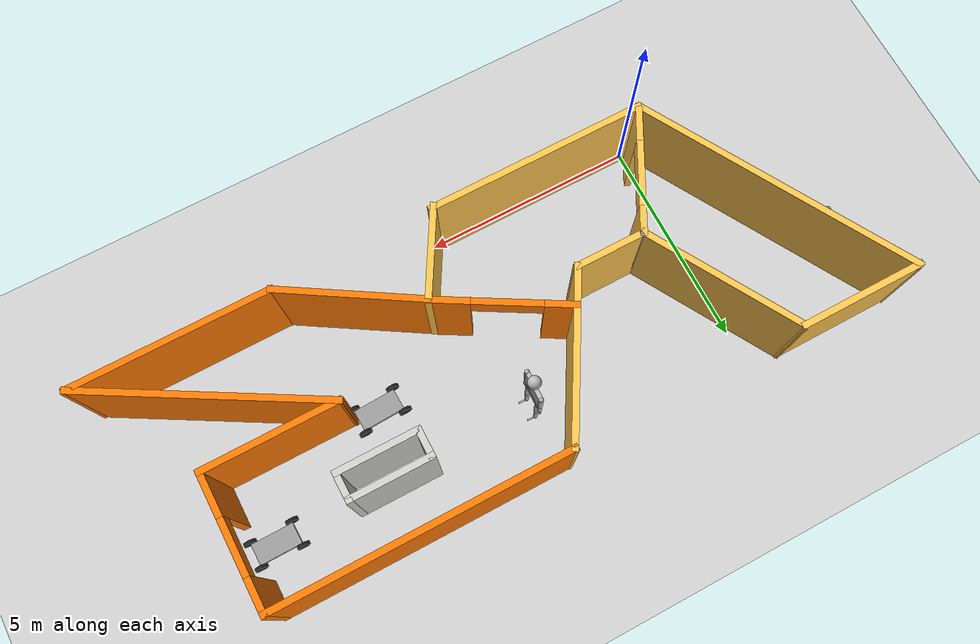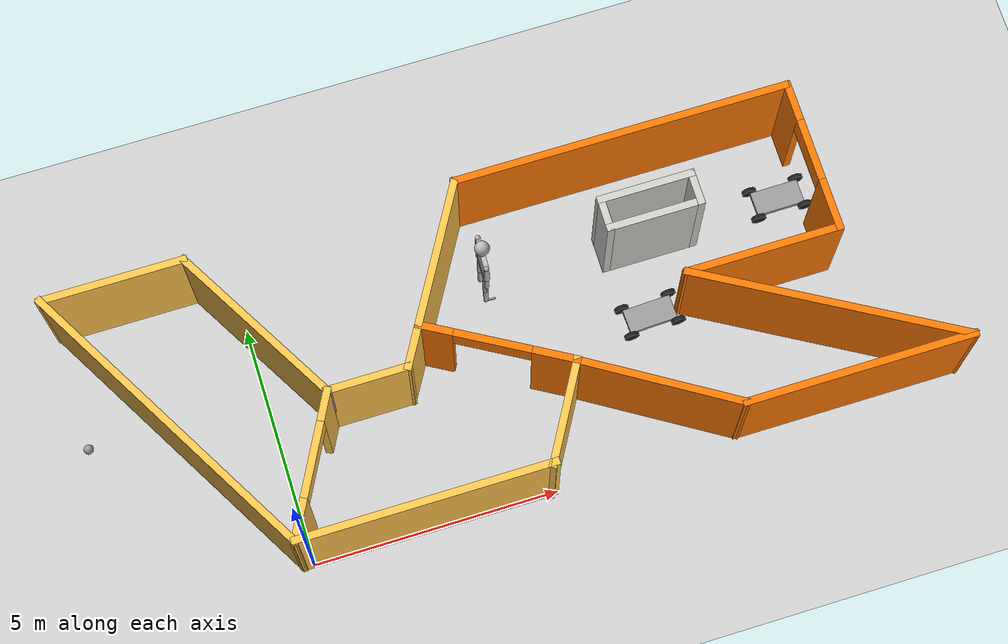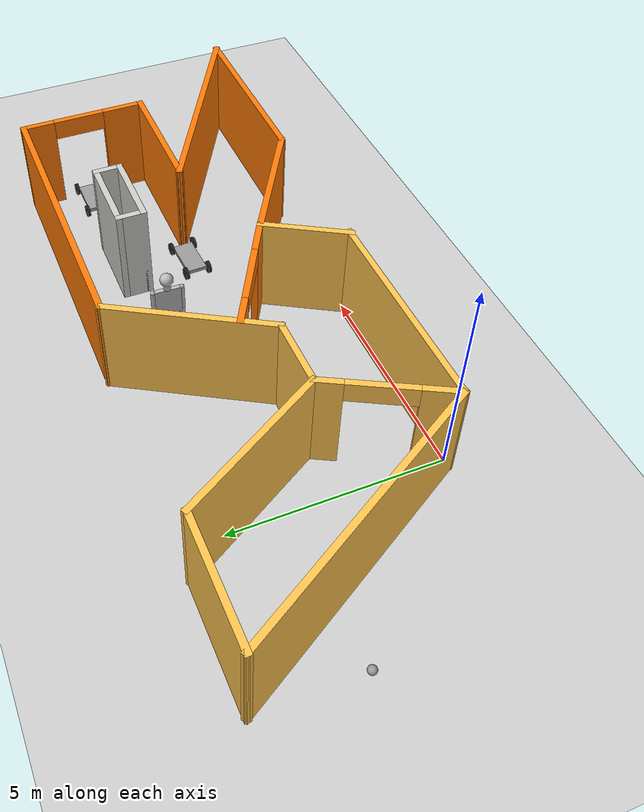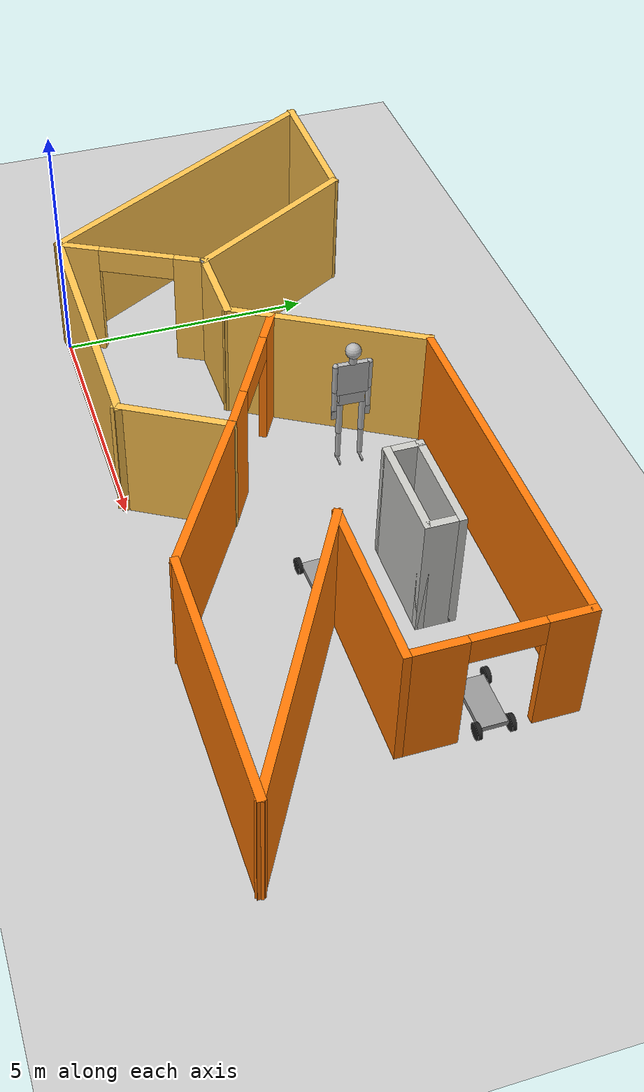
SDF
<sdf version="1.6">
 <world name="default">
  <plugin filename="libcollision_map_creator.so" name="collision_map_creator"/>
  <plugin name="welcome" filename="libwelcome_message.so"/>
  <light name="sun" type="directional">
   <pose>0 0 10 0 -0 0</pose>
   <diffuse>0.8 0.8 0.8 1</diffuse>
   <specular>0.2 0.2 0.2 1</specular>
   <attenuation>
    <range>1000</range>
    <constant>0.9</constant>
    <linear>0.01</linear>
    <quadratic>0.001</quadratic>
   </attenuation>
   <direction>-0.5 0.1 -0.9</direction>
   <spot><inner_angle>0</inner_angle><outer_angle>0</outer_angle><falloff>0</falloff></spot>
  </light>
  <model name="ground_plane">
   <pose>0 0 0 0 -0 0.3</pose>
   <static>1</static>
   <link name="link">
    <collision name="collision">
     <geometry><plane><normal>0 0 1</normal><size>100 100</size></plane></geometry>
     <surface>
      <contact><collide_bitmask>65535</collide_bitmask></contact>
      <friction><ode><mu>100</mu><mu2>50</mu2></ode></friction>
     </surface>
    </collision>
    <visual name="visual">
     <cast_shadows>0</cast_shadows>
     <geometry><plane><normal>0 0 1</normal><size>100 100</size></plane></geometry>
     <material>
      <script><uri>file://media/materials/scripts/gazebo.material</uri><name>Gazebo/Grey</name></script>
     </material>
    </visual>
   </link>
  </model>
  <gravity>0 0 -9.8</gravity>
  <magnetic_field>6e-06 2.3e-05 -4.2e-05</magnetic_field>
  <atmosphere type="adiabatic"/>
  <physics name="default_physics" default="0" type="ode">
   <max_step_size>0.001</max_step_size>
   <real_time_factor>1</real_time_factor>
   <real_time_update_rate>1000</real_time_update_rate>
  </physics>
  <scene><ambient>0.4 0.4 0.4 1</ambient><background>0.7 0.7 0.7 1</background><shadows>1</shadows></scene>
  <audio><device>default</device></audio>
  <spherical_coordinates>
   <surface_model>EARTH_WGS84</surface_model>
   <latitude_deg>0</latitude_deg>
   <longitude_deg>0</longitude_deg>
   <elevation>0</elevation>
   <heading_deg>0</heading_deg>
  </spherical_coordinates>
  <model name="model">
   <pose>4.86441 3.63038 0 0 -0 0</pose>
   <link name="Wall_1">
    <collision name="Wall_1_Collision">
     <geometry><box><size>3 0.15 2.5</size></box></geometry>
     <pose>0 0 1.25 0 -0 0</pose>
    </collision>
    <visual name="Wall_1_Visual">
     <pose>0 0 1.25 0 -0 0</pose>
     <geometry><box><size>3 0.15 2.5</size></box></geometry>
     <material>
      <script><uri>file://media/materials/scripts/gazebo.material</uri><name>Gazebo/Grey</name></script>
      <ambient>1 0.764706 0.305882 1</ambient>
     </material>
     <meta><layer>0</layer></meta>
    </visual>
    <pose>-7.02494 2.33089 0 0 -0 0</pose>
   </link>
   <link name="Wall_10">
    <collision name="Wall_10_Collision">
     <geometry><box><size>3.45374 0.15 2.5</size></box></geometry>
     <pose>0 0 1.25 0 -0 0</pose>
    </collision>
    <visual name="Wall_10_Visual">
     <pose>0 0 1.25 0 -0 0</pose>
     <geometry><box><size>3.45374 0.15 2.5</size></box></geometry>
     <material>
      <script><uri>file://media/materials/scripts/gazebo.material</uri><name>Gazebo/Grey</name></script>
      <ambient>0.996078 0.47451 0.0196078 1</ambient>
     </material>
     <meta><layer>0</layer></meta>
    </visual>
    <pose>2.44495 -2.70017 0 0 -0 2.58766</pose>
   </link>
   <link name="Wall_11">
    <collision name="Wall_11_Collision">
     <geometry><box><size>2.25 0.15 2.5</size></box></geometry>
     <pose>0 0 1.25 0 -0 0</pose>
    </collision>
    <visual name="Wall_11_Visual">
     <pose>0 0 1.25 0 -0 0</pose>
     <geometry><box><size>2.25 0.15 2.5</size></box></geometry>
     <material>
      <script><uri>file://media/materials/scripts/gazebo.material</uri><name>Gazebo/Grey</name></script>
      <ambient>1 0.764706 0.305882 1</ambient>
     </material>
     <meta><layer>0</layer></meta>
    </visual>
    <pose>0.5151 -2.72911 0 0 -0 -2.0944</pose>
   </link>
   <link name="Wall_2">
    <collision name="Wall_2_Collision">
     <geometry><box><size>4 0.15 2.5</size></box></geometry>
     <pose>0 0 1.25 0 -0 0</pose>
    </collision>
    <visual name="Wall_2_Visual">
     <pose>0 0 1.25 0 -0 0</pose>
     <geometry><box><size>4 0.15 2.5</size></box></geometry>
     <material>
      <script><uri>file://media/materials/scripts/gazebo.material</uri><name>Gazebo/Grey</name></script>
      <ambient>1 0.764706 0.305882 1</ambient>
     </material>
     <meta><layer>0</layer></meta>
    </visual>
    <pose>-4.63744 0.66379 0 0 -0 -1.0472</pose>
   </link>
   <link name="Wall_20">
    <collision name="Wall_20_Collision">
     <geometry><box><size>6.98788 0.15 2.5</size></box></geometry>
     <pose>0 0 1.25 0 -0 0</pose>
    </collision>
    <visual name="Wall_20_Visual">
     <pose>0 0 1.25 0 -0 0</pose>
     <geometry><box><size>6.98788 0.15 2.5</size></box></geometry>
     <material>
      <script><uri>file://media/materials/scripts/gazebo.material</uri><name>Gazebo/Grey</name></script>
      <ambient>1 0.764706 0.305882 1</ambient>
     </material>
     <meta><layer>0</layer></meta>
    </visual>
    <pose>-6.75459 -0.638107 0 0 -0 -1.05196</pose>
   </link>
   <link name="Wall_21">
    <collision name="Wall_21_Collision">
     <geometry><box><size>5.25 0.15 2.5</size></box></geometry>
     <pose>0 0 1.25 0 -0 0</pose>
    </collision>
    <visual name="Wall_21_Visual">
     <pose>0 0 1.25 0 -0 0</pose>
     <geometry><box><size>5.25 0.15 2.5</size></box></geometry>
     <material>
      <script><uri>file://media/materials/scripts/gazebo.material</uri><name>Gazebo/Grey</name></script>
      <ambient>1 0.764706 0.305882 1</ambient>
     </material>
     <meta><layer>0</layer></meta>
    </visual>
    <pose>-2.49781 -3.6071 0 0 -0 0</pose>
   </link>
   <link name="Wall_23">
    <collision name="Wall_23_Collision">
     <geometry><box><size>2 0.15 2.5</size></box></geometry>
     <pose>0 0 1.25 0 -0 0</pose>
    </collision>
    <visual name="Wall_23_Visual">
     <pose>0 0 1.25 0 -0 0</pose>
     <geometry><box><size>2 0.15 2.5</size></box></geometry>
     <material>
      <script><uri>file://media/materials/scripts/gazebo.material</uri><name>Gazebo/CeilingTiled</name></script>
      <ambient>0.435294 0.796078 0.67451 1</ambient>
     </material>
     <meta><layer>0</layer></meta>
    </visual>
    <pose>3.37989 1.12451 0 0 -0 3.14159</pose>
   </link>
   <link name="Wall_24">
    <collision name="Wall_24_Collision">
     <geometry><box><size>0.75 0.15 2.5</size></box></geometry>
     <pose>0 0 1.25 0 -0 0</pose>
    </collision>
    <visual name="Wall_24_Visual">
     <pose>0 0 1.25 0 -0 0</pose>
     <geometry><box><size>0.75 0.15 2.5</size></box></geometry>
     <material>
      <script><uri>file://media/materials/scripts/gazebo.material</uri><name>Gazebo/CeilingTiled</name></script>
      <ambient>0.435294 0.796078 0.67451 1</ambient>
     </material>
     <meta><layer>0</layer></meta>
    </visual>
    <pose>2.45489 0.824511 0 0 -0 -1.5708</pose>
   </link>
   <link name="Wall_25">
    <collision name="Wall_25_Collision">
     <geometry><box><size>2 0.15 2.5</size></box></geometry>
     <pose>0 0 1.25 0 -0 0</pose>
    </collision>
    <visual name="Wall_25_Visual">
     <pose>0 0 1.25 0 -0 0</pose>
     <geometry><box><size>2 0.15 2.5</size></box></geometry>
     <material>
      <script><uri>file://media/materials/scripts/gazebo.material</uri><name>Gazebo/CeilingTiled</name></script>
      <ambient>0.435294 0.796078 0.67451 1</ambient>
     </material>
     <meta><layer>0</layer></meta>
    </visual>
    <pose>3.37989 0.524511 0 0 -0 0</pose>
   </link>
   <link name="Wall_26">
    <collision name="Wall_26_Collision">
     <geometry><box><size>0.75 0.15 2.5</size></box></geometry>
     <pose>0 0 1.25 0 -0 0</pose>
    </collision>
    <visual name="Wall_26_Visual">
     <pose>0 0 1.25 0 -0 0</pose>
     <geometry><box><size>0.75 0.15 2.5</size></box></geometry>
     <material>
      <script><uri>file://media/materials/scripts/gazebo.material</uri><name>Gazebo/CeilingTiled</name></script>
      <ambient>0.435294 0.796078 0.67451 1</ambient>
     </material>
     <meta><layer>0</layer></meta>
    </visual>
    <pose>4.30489 0.824511 0 0 -0 1.5708</pose>
   </link>
   <link name="Wall_28">
    <collision name="Wall_28_Collision">
     <geometry><box><size>0.15 0.15 2.5</size></box></geometry>
     <pose>0 0 1.25 0 -0 0</pose>
    </collision>
    <visual name="Wall_28_Visual">
     <pose>0 0 1.25 0 -0 0</pose>
     <geometry><box><size>0.15 0.15 2.5</size></box></geometry>
     <material>
      <script><uri>file://media/materials/scripts/gazebo.material</uri><name>Gazebo/Grey</name></script>
      <ambient>1 1 1 1</ambient>
     </material>
     <meta><layer>0</layer></meta>
    </visual>
    <pose>-3.67494 -1.00331 0 0 -0 0</pose>
   </link>
   <link name="Wall_29">
    <pose>-4.36137 -2.30521 0 0 -0 -2.05601</pose>
    <visual name="Wall_29_Visual_0">
     <pose>-1.20446 0 1.25 0 -0 0</pose>
     <geometry><box><size>0.684636 0.15 2.5</size></box></geometry>
     <material>
      <script><uri>file://media/materials/scripts/gazebo.material</uri><name>Gazebo/Grey</name></script>
      <ambient>1 0.764706 0.305882 1</ambient>
     </material>
     <meta><layer>0</layer></meta>
    </visual>
    <collision name="Wall_29_Collision_0">
     <geometry><box><size>0.684636 0.15 2.5</size></box></geometry>
     <pose>-1.20446 0 1.25 0 -0 0</pose>
    </collision>
    <visual name="Wall_29_Visual_1">
     <pose>1.09942 0 1.25 0 -0 0</pose>
     <geometry><box><size>0.894721 0.15 2.5</size></box></geometry>
     <material>
      <script><uri>file://media/materials/scripts/gazebo.material</uri><name>Gazebo/Grey</name></script>
      <ambient>1 0.764706 0.305882 1</ambient>
     </material>
     <meta><layer>0</layer></meta>
    </visual>
    <collision name="Wall_29_Collision_1">
     <geometry><box><size>0.894721 0.15 2.5</size></box></geometry>
     <pose>1.09942 0 1.25 0 -0 0</pose>
    </collision>
    <visual name="Wall_29_Visual_2">
     <pose>-0.105042 0 2.25 0 -0 0</pose>
     <geometry><box><size>1.5142 0.15 0.5</size></box></geometry>
     <material>
      <script><uri>file://media/materials/scripts/gazebo.material</uri><name>Gazebo/Grey</name></script>
      <ambient>1 0.764706 0.305882 1</ambient>
     </material>
     <meta><layer>0</layer></meta>
    </visual>
    <collision name="Wall_29_Collision_2">
     <geometry><box><size>1.5142 0.15 0.5</size></box></geometry>
     <pose>-0.105042 0 2.25 0 -0 0</pose>
    </collision>
   </link>
   <link name="Wall_3">
    <collision name="Wall_3_Collision">
     <geometry><box><size>1.75 0.15 2.5</size></box></geometry>
     <pose>0 0 1.25 0 -0 0</pose>
    </collision>
    <visual name="Wall_3_Visual">
     <pose>0 0 1.25 0 -0 0</pose>
     <geometry><box><size>1.75 0.15 2.5</size></box></geometry>
     <material>
      <script><uri>file://media/materials/scripts/gazebo.material</uri><name>Gazebo/Grey</name></script>
      <ambient>1 0.764706 0.305882 1</ambient>
     </material>
     <meta><layer>0</layer></meta>
    </visual>
    <pose>-2.87494 -1.00331 0 0 -0 0</pose>
   </link>
   <link name="Wall_32">
    <pose>-0.302239 -1.04478 0 0 -0 2.61799</pose>
    <visual name="Wall_32_Visual_0">
     <pose>-1.15002 0 1.25 0 -0 0</pose>
     <geometry><box><size>0.949952 0.15 2.5</size></box></geometry>
     <material>
      <script><uri>file://media/materials/scripts/gazebo.material</uri><name>Gazebo/Grey</name></script>
      <ambient>0.996078 0.47451 0.0196078 1</ambient>
     </material>
     <meta><layer>0</layer></meta>
    </visual>
    <collision name="Wall_32_Collision_0">
     <geometry><box><size>0.949952 0.15 2.5</size></box></geometry>
     <pose>-1.15002 0 1.25 0 -0 0</pose>
    </collision>
    <visual name="Wall_32_Visual_1">
     <pose>1.24923 0 1.25 0 -0 0</pose>
     <geometry><box><size>0.751532 0.15 2.5</size></box></geometry>
     <material>
      <script><uri>file://media/materials/scripts/gazebo.material</uri><name>Gazebo/Grey</name></script>
      <ambient>0.996078 0.47451 0.0196078 1</ambient>
     </material>
     <meta><layer>0</layer></meta>
    </visual>
    <collision name="Wall_32_Collision_1">
     <geometry><box><size>0.751532 0.15 2.5</size></box></geometry>
     <pose>1.24923 0 1.25 0 -0 0</pose>
    </collision>
    <visual name="Wall_32_Visual_2">
     <pose>0.09921 0 2.25 0 -0 0</pose>
     <geometry><box><size>1.54852 0.15 0.5</size></box></geometry>
     <material>
      <script><uri>file://media/materials/scripts/gazebo.material</uri><name>Gazebo/Grey</name></script>
      <ambient>0.996078 0.47451 0.0196078 1</ambient>
     </material>
     <meta><layer>0</layer></meta>
    </visual>
    <collision name="Wall_32_Collision_2">
     <geometry><box><size>1.54852 0.15 0.5</size></box></geometry>
     <pose>0.09921 0 2.25 0 -0 0</pose>
    </collision>
   </link>
   <link name="Wall_4">
    <collision name="Wall_4_Collision">
     <geometry><box><size>4 0.15 2.5</size></box></geometry>
     <pose>0 0 1.25 0 -0 0</pose>
    </collision>
    <visual name="Wall_4_Visual">
     <pose>0 0 1.25 0 -0 0</pose>
     <geometry><box><size>4 0.15 2.5</size></box></geometry>
     <material>
      <script><uri>file://media/materials/scripts/gazebo.material</uri><name>Gazebo/Grey</name></script>
      <ambient>1 0.764706 0.305882 1</ambient>
     </material>
     <meta><layer>0</layer></meta>
    </visual>
    <pose>-1.11244 0.66379 0 0 -0 1.0472</pose>
   </link>
   <link name="Wall_5">
    <collision name="Wall_5_Collision">
     <geometry><box><size>7 0.15 2.5</size></box></geometry>
     <pose>0 0 1.25 0 -0 0</pose>
    </collision>
    <visual name="Wall_5_Visual">
     <pose>0 0 1.25 0 -0 0</pose>
     <geometry><box><size>7 0.15 2.5</size></box></geometry>
     <material>
      <script><uri>file://media/materials/scripts/gazebo.material</uri><name>Gazebo/Grey</name></script>
      <ambient>0.996078 0.47451 0.0196078 1</ambient>
     </material>
     <meta><layer>0</layer></meta>
    </visual>
    <pose>3.27506 2.33089 0 0 -0 0</pose>
   </link>
   <link name="Wall_6">
    <pose>6.70006 0.780889 0 0 -0 -1.5708</pose>
    <visual name="Wall_6_Visual_0">
     <pose>-1.19377 0 1.25 0 -0 0</pose>
     <geometry><box><size>0.862464 0.15 2.5</size></box></geometry>
     <material>
      <script><uri>file://media/materials/scripts/gazebo.material</uri><name>Gazebo/Grey</name></script>
      <ambient>0.996078 0.47451 0.0196078 1</ambient>
     </material>
     <meta><layer>0</layer></meta>
    </visual>
    <collision name="Wall_6_Collision_0">
     <geometry><box><size>0.862464 0.15 2.5</size></box></geometry>
     <pose>-1.19377 0 1.25 0 -0 0</pose>
    </collision>
    <visual name="Wall_6_Visual_1">
     <pose>1.07673 0 1.25 0 -0 0</pose>
     <geometry><box><size>1.09654 0.15 2.5</size></box></geometry>
     <material>
      <script><uri>file://media/materials/scripts/gazebo.material</uri><name>Gazebo/Grey</name></script>
      <ambient>0.996078 0.47451 0.0196078 1</ambient>
     </material>
     <meta><layer>0</layer></meta>
    </visual>
    <collision name="Wall_6_Collision_1">
     <geometry><box><size>1.09654 0.15 2.5</size></box></geometry>
     <pose>1.07673 0 1.25 0 -0 0</pose>
    </collision>
    <visual name="Wall_6_Visual_2">
     <pose>-0.117036 0 2.25 0 -0 0</pose>
     <geometry><box><size>1.291 0.15 0.5</size></box></geometry>
     <material>
      <script><uri>file://media/materials/scripts/gazebo.material</uri><name>Gazebo/Grey</name></script>
      <ambient>0.996078 0.47451 0.0196078 1</ambient>
     </material>
     <meta><layer>0</layer></meta>
    </visual>
    <collision name="Wall_6_Collision_2">
     <geometry><box><size>1.291 0.15 0.5</size></box></geometry>
     <pose>-0.117036 0 2.25 0 -0 0</pose>
    </collision>
   </link>
   <link name="Wall_7">
    <collision name="Wall_7_Collision">
     <geometry><box><size>3.25 0.15 2.5</size></box></geometry>
     <pose>0 0 1.25 0 -0 0</pose>
    </collision>
    <visual name="Wall_7_Visual">
     <pose>0 0 1.25 0 -0 0</pose>
     <geometry><box><size>3.25 0.15 2.5</size></box></geometry>
     <material>
      <script><uri>file://media/materials/scripts/gazebo.material</uri><name>Gazebo/Grey</name></script>
      <ambient>0.996078 0.47451 0.0196078 1</ambient>
     </material>
     <meta><layer>0</layer></meta>
    </visual>
    <pose>5.15006 -0.769112 0 0 -0 3.14159</pose>
   </link>
   <link name="Wall_8">
    <collision name="Wall_8_Collision">
     <geometry><box><size>5.75 0.15 2.5</size></box></geometry>
     <pose>0 0 1.25 0 -0 0</pose>
    </collision>
    <visual name="Wall_8_Visual">
     <pose>0 0 1.25 0 -0 0</pose>
     <geometry><box><size>5.75 0.15 2.5</size></box></geometry>
     <material>
      <script><uri>file://media/materials/scripts/gazebo.material</uri><name>Gazebo/Grey</name></script>
      <ambient>0.996078 0.47451 0.0196078 1</ambient>
     </material>
     <meta><layer>0</layer></meta>
    </visual>
    <pose>6.02493 -2.16911 0 0 -0 -0.523599</pose>
   </link>
   <link name="Wall_9">
    <collision name="Wall_9_Collision">
     <geometry><box><size>4.75 0.15 2.5</size></box></geometry>
     <pose>0 0 1.25 0 -0 0</pose>
    </collision>
    <visual name="Wall_9_Visual">
     <pose>0 0 1.25 0 -0 0</pose>
     <geometry><box><size>4.75 0.15 2.5</size></box></geometry>
     <material>
      <script><uri>file://media/materials/scripts/gazebo.material</uri><name>Gazebo/Grey</name></script>
      <ambient>0.996078 0.47451 0.0196078 1</ambient>
     </material>
     <meta><layer>0</layer></meta>
    </visual>
    <pose>6.1498 -3.56911 0 0 -0 3.14159</pose>
   </link>
   <static>1</static>
  </model>
  <model name="model_1">
   <model name="cart_front_steer">
    <link name="chassis">
     <pose>0 0 0.15 0 -0 0</pose>
     <inertial>
      <pose>0.1 0 0 0 -0 0</pose>
      <mass>10</mass>
      <inertia>
       <ixx>0.216667</ixx>
       <iyy>0.841667</iyy>
       <izz>1.04167</izz>
       <ixy>0</ixy>
       <ixz>0</ixz>
       <iyz>0</iyz>
      </inertia>
     </inertial>
     <collision name="collision"><geometry><box><size>1 0.5 0.1</size></box></geometry></collision>
     <visual name="visual">
      <geometry><box><size>1 0.5 0.1</size></box></geometry>
      <material>
       <script><uri>file://media/materials/scripts/gazebo.material</uri><name>Gazebo/Grey</name></script>
      </material>
     </visual>
    </link>
    <link name="wheel_front_left">
     <pose>0.5 0.298 0.15 -1.5708 -0.087266 0</pose>
     <inertial>
      <mass>0.5</mass>
      <inertia>
       <ixx>0.00307917</ixx>
       <iyy>0.00307917</iyy>
       <izz>0.005625</izz>
       <ixy>0</ixy>
       <ixz>0</ixz>
       <iyz>0</iyz>
      </inertia>
     </inertial>
     <collision name="collision">
      <geometry><cylinder><radius>0.15</radius><length>0.08</length></cylinder></geometry>
     </collision>
     <visual name="visual">
      <geometry><cylinder><radius>0.15</radius><length>0.08</length></cylinder></geometry>
      <material>
       <script><uri>file://media/materials/scripts/gazebo.material</uri><name>Gazebo/Black</name></script>
      </material>
     </visual>
    </link>
    <joint name="wheel_front_left_steer_spin" type="universal">
     <parent>chassis</parent>
     <child>wheel_front_left</child>
     <axis>
      <xyz>0 -1 0</xyz>
      <limit><lower>-0.610865</lower><upper>0.610865</upper></limit>
      <dynamics><spring_reference>0</spring_reference><spring_stiffness>0</spring_stiffness></dynamics>
      <use_parent_model_frame>0</use_parent_model_frame>
     </axis>
     <axis2>
      <xyz>0 0 1</xyz>
      <limit><upper>1e+16</upper><lower>-1e+16</lower></limit>
      <dynamics><spring_reference>0</spring_reference><spring_stiffness>0</spring_stiffness></dynamics>
      <use_parent_model_frame>0</use_parent_model_frame>
     </axis2>
    </joint>
    <link name="wheel_front_right">
     <pose>0.5 -0.298 0.15 -1.5708 -0.087266 0</pose>
     <inertial>
      <mass>0.5</mass>
      <inertia>
       <ixx>0.00307917</ixx>
       <iyy>0.00307917</iyy>
       <izz>0.005625</izz>
       <ixy>0</ixy>
       <ixz>0</ixz>
       <iyz>0</iyz>
      </inertia>
     </inertial>
     <collision name="collision">
      <geometry><cylinder><radius>0.15</radius><length>0.08</length></cylinder></geometry>
     </collision>
     <visual name="visual">
      <geometry><cylinder><radius>0.15</radius><length>0.08</length></cylinder></geometry>
      <material>
       <script><uri>file://media/materials/scripts/gazebo.material</uri><name>Gazebo/Black</name></script>
      </material>
     </visual>
    </link>
    <joint name="wheel_front_right_steer_spin" type="universal">
     <parent>chassis</parent>
     <child>wheel_front_right</child>
     <axis>
      <xyz>0 -1 0</xyz>
      <limit><lower>-0.610865</lower><upper>0.610865</upper></limit>
      <dynamics><spring_reference>0</spring_reference><spring_stiffness>0</spring_stiffness></dynamics>
      <use_parent_model_frame>0</use_parent_model_frame>
     </axis>
     <axis2>
      <xyz>0 0 1</xyz>
      <limit><upper>1e+16</upper><lower>-1e+16</lower></limit>
      <dynamics><spring_reference>0</spring_reference><spring_stiffness>0</spring_stiffness></dynamics>
      <use_parent_model_frame>0</use_parent_model_frame>
     </axis2>
    </joint>
    <link name="wheel_rear_left">
     <pose>-0.5 0.298 0.15 -1.5708 0 0</pose>
     <inertial>
      <mass>0.5</mass>
      <inertia>
       <ixx>0.00307917</ixx>
       <iyy>0.00307917</iyy>
       <izz>0.005625</izz>
       <ixy>0</ixy>
       <ixz>0</ixz>
       <iyz>0</iyz>
      </inertia>
     </inertial>
     <collision name="collision">
      <geometry><cylinder><radius>0.15</radius><length>0.08</length></cylinder></geometry>
     </collision>
     <visual name="visual">
      <geometry><cylinder><radius>0.15</radius><length>0.08</length></cylinder></geometry>
      <material>
       <script><uri>file://media/materials/scripts/gazebo.material</uri><name>Gazebo/Black</name></script>
      </material>
     </visual>
    </link>
    <joint name="wheel_rear_left_spin" type="revolute">
     <parent>chassis</parent>
     <child>wheel_rear_left</child>
     <axis>
      <xyz>0 0 1</xyz>
      <limit><lower>-1e+16</lower><upper>1e+16</upper></limit>
      <dynamics><spring_reference>0</spring_reference><spring_stiffness>0</spring_stiffness></dynamics>
      <use_parent_model_frame>0</use_parent_model_frame>
     </axis>
    </joint>
    <link name="wheel_rear_right">
     <pose>-0.5 -0.298 0.15 -1.5708 0 0</pose>
     <inertial>
      <mass>0.5</mass>
      <inertia>
       <ixx>0.00307917</ixx>
       <iyy>0.00307917</iyy>
       <izz>0.005625</izz>
       <ixy>0</ixy>
       <ixz>0</ixz>
       <iyz>0</iyz>
      </inertia>
     </inertial>
     <collision name="collision">
      <geometry><cylinder><radius>0.15</radius><length>0.08</length></cylinder></geometry>
     </collision>
     <visual name="visual">
      <geometry><cylinder><radius>0.15</radius><length>0.08</length></cylinder></geometry>
      <material>
       <script><uri>file://media/materials/scripts/gazebo.material</uri><name>Gazebo/Black</name></script>
      </material>
     </visual>
    </link>
    <joint name="wheel_rear_right_spin" type="revolute">
     <parent>chassis</parent>
     <child>wheel_rear_right</child>
     <axis>
      <xyz>0 0 1</xyz>
      <limit><lower>-1e+16</lower><upper>1e+16</upper></limit>
      <dynamics><spring_reference>0</spring_reference><spring_stiffness>0</spring_stiffness></dynamics>
      <use_parent_model_frame>0</use_parent_model_frame>
     </axis>
    </joint>
    <pose>-1.06061 0.576576 0 0 -0 0</pose>
   </model>
   <static>0</static>
   <allow_auto_disable>0</allow_auto_disable>
   <pose>8.94203 2.37104 8e-06 -1.6e-05 -1e-06 0.04098</pose>
  </model>
  <model name="ragdoll">
   <pose>4.81268 4.42847 1.39996 1.2e-05 0.00064 -0.037719</pose>
   <link name="hip">
    <inertial>
     <inertia><ixx>0.1</ixx><ixy>0</ixy><ixz>0</ixz><iyy>0.1</iyy><iyz>0</iyz><izz>0.1</izz></inertia>
     <mass>10</mass>
    </inertial>
    <collision name="hip_geom">
     <pose>0 0 0.125 0 -0 0</pose>
     <geometry><box><size>0.1 0.5 0.25</size></box></geometry>
     <surface>
      <friction><ode><mu>-1</mu><mu2>-1</mu2><fdir1>0 0 0</fdir1><slip1>0</slip1><slip2>0</slip2></ode></friction>
      <bounce><restitution_coefficient>0</restitution_coefficient><threshold>100000</threshold></bounce>
      <contact>
       <ode>
        <soft_cfm>0</soft_cfm>
        <soft_erp>0.2</soft_erp>
        <kp>1e+12</kp>
        <kd>1</kd>
        <max_vel>0</max_vel>
        <min_depth>0.001</min_depth>
       </ode>
      </contact>
     </surface>
    </collision>
    <visual name="hip_geom_visual">
     <pose>0 0 0.125 0 -0 0</pose>
     <geometry><box><size>0.1 0.5 0.25</size></box></geometry>
    </visual>
    <gravity>0</gravity>
   </link>
   <link name="l_thigh_pan">
    <pose>0 0.22 0 0 -0 0</pose>
    <inertial>
     <inertia><ixx>0.01</ixx><ixy>0</ixy><ixz>0</ixz><iyy>0.01</iyy><iyz>0</iyz><izz>0.01</izz></inertia>
     <mass>1</mass>
    </inertial>
    <collision name="l_thigh_pan_geom">
     <pose>0 0 -0.03 0 -0 0</pose>
     <geometry><sphere><radius>0.06</radius></sphere></geometry>
     <surface>
      <friction><ode><mu>-1</mu><mu2>-1</mu2><fdir1>0 0 0</fdir1><slip1>0</slip1><slip2>0</slip2></ode></friction>
      <bounce><restitution_coefficient>0</restitution_coefficient><threshold>100000</threshold></bounce>
      <contact>
       <ode>
        <soft_cfm>0</soft_cfm>
        <soft_erp>0.2</soft_erp>
        <kp>1e+12</kp>
        <kd>1</kd>
        <max_vel>0</max_vel>
        <min_depth>0.001</min_depth>
       </ode>
      </contact>
     </surface>
    </collision>
    <visual name="l_thigh_pan_geom_visual">
     <pose>0 0 -0.03 0 -0 0</pose>
     <geometry><sphere><radius>0.06</radius></sphere></geometry>
    </visual>
    <gravity>0</gravity>
   </link>
   <link name="l_thigh_lift">
    <pose>0 0.22 0 0 -0 0</pose>
    <inertial>
     <inertia><ixx>0.05</ixx><ixy>0</ixy><ixz>0</ixz><iyy>0.05</iyy><iyz>0</iyz><izz>0.05</izz></inertia>
     <mass>5</mass>
    </inertial>
    <collision name="l_thigh_lift_geom">
     <pose>0 0 -0.35 0 -0 0</pose>
     <geometry><cylinder><radius>0.06</radius><length>0.7</length></cylinder></geometry>
     <surface>
      <friction><ode><mu>-1</mu><mu2>-1</mu2><fdir1>0 0 0</fdir1><slip1>0</slip1><slip2>0</slip2></ode></friction>
      <bounce><restitution_coefficient>0</restitution_coefficient><threshold>100000</threshold></bounce>
      <contact>
       <ode>
        <soft_cfm>0</soft_cfm>
        <soft_erp>0.2</soft_erp>
        <kp>1e+12</kp>
        <kd>1</kd>
        <max_vel>0</max_vel>
        <min_depth>0.001</min_depth>
       </ode>
      </contact>
     </surface>
    </collision>
    <visual name="l_thigh_lift_geom_visual">
     <pose>0 0 -0.35 0 -0 0</pose>
     <geometry><cylinder><radius>0.06</radius><length>0.7</length></cylinder></geometry>
    </visual>
    <gravity>0</gravity>
   </link>
   <link name="l_calf">
    <pose>0 0.22 -0.7 0 -0 0</pose>
    <inertial>
     <inertia><ixx>0.02</ixx><ixy>0</ixy><ixz>0</ixz><iyy>0.02</iyy><iyz>0</iyz><izz>0.02</izz></inertia>
     <mass>2</mass>
    </inertial>
    <collision name="l_calf_geom">
     <pose>0 0 -0.3 0 -0 0</pose>
     <geometry><cylinder><radius>0.05</radius><length>0.6</length></cylinder></geometry>
     <surface>
      <friction><ode><mu>-1</mu><mu2>-1</mu2><fdir1>0 0 0</fdir1><slip1>0</slip1><slip2>0</slip2></ode></friction>
      <bounce><restitution_coefficient>0</restitution_coefficient><threshold>100000</threshold></bounce>
      <contact>
       <ode>
        <soft_cfm>0</soft_cfm>
        <soft_erp>0.2</soft_erp>
        <kp>1e+12</kp>
        <kd>1</kd>
        <max_vel>0</max_vel>
        <min_depth>0.001</min_depth>
       </ode>
      </contact>
     </surface>
    </collision>
    <visual name="l_calf_geom_visual">
     <pose>0 0 -0.3 0 -0 0</pose>
     <geometry><cylinder><radius>0.05</radius><length>0.6</length></cylinder></geometry>
    </visual>
    <gravity>0</gravity>
   </link>
   <link name="l_ankle">
    <pose>0 0.22 -1.325 0 -0 0</pose>
    <inertial>
     <inertia><ixx>0.01</ixx><ixy>0</ixy><ixz>0</ixz><iyy>0.01</iyy><iyz>0</iyz><izz>0.01</izz></inertia>
     <mass>1</mass>
    </inertial>
    <collision name="l_ankle_geom">
     <geometry><sphere><radius>0.05</radius></sphere></geometry>
     <surface>
      <friction><ode><mu>-1</mu><mu2>-1</mu2><fdir1>0 0 0</fdir1><slip1>0</slip1><slip2>0</slip2></ode></friction>
      <bounce><restitution_coefficient>0</restitution_coefficient><threshold>100000</threshold></bounce>
      <contact>
       <ode>
        <soft_cfm>0</soft_cfm>
        <soft_erp>0.2</soft_erp>
        <kp>1e+12</kp>
        <kd>1</kd>
        <max_vel>0</max_vel>
        <min_depth>0.001</min_depth>
       </ode>
      </contact>
     </surface>
    </collision>
    <visual name="l_ankle_geom_visual"><geometry><sphere><radius>0.05</radius></sphere></geometry></visual>
    <gravity>0</gravity>
   </link>
   <link name="l_foot">
    <pose>0 0.22 -1.35 0 -0 0</pose>
    <inertial>
     <pose>0.1 0 0 0 -0 0</pose>
     <inertia><ixx>0.01</ixx><ixy>0</ixy><ixz>0</ixz><iyy>0.01</iyy><iyz>0</iyz><izz>0.01</izz></inertia>
     <mass>1</mass>
    </inertial>
    <collision name="l_foot_geom">
     <pose>0.1 0 -0.025 0 -0 0</pose>
     <geometry><box><size>0.2 0.03 0.05</size></box></geometry>
     <surface>
      <friction><ode><mu>-1</mu><mu2>-1</mu2><fdir1>0 0 0</fdir1><slip1>0</slip1><slip2>0</slip2></ode></friction>
      <bounce><restitution_coefficient>0</restitution_coefficient><threshold>100000</threshold></bounce>
      <contact>
       <ode>
        <soft_cfm>0</soft_cfm>
        <soft_erp>0.2</soft_erp>
        <kp>1e+12</kp>
        <kd>1</kd>
        <max_vel>0</max_vel>
        <min_depth>0.001</min_depth>
       </ode>
      </contact>
     </surface>
    </collision>
    <visual name="l_foot_geom_visual">
     <pose>0.1 0 -0.025 0 -0 0</pose>
     <geometry><box><size>0.2 0.03 0.05</size></box></geometry>
    </visual>
   </link>
   <link name="r_thigh_pan">
    <pose>0 -0.22 0 0 -0 0</pose>
    <inertial>
     <inertia><ixx>0.01</ixx><ixy>0</ixy><ixz>0</ixz><iyy>0.01</iyy><iyz>0</iyz><izz>0.01</izz></inertia>
     <mass>1</mass>
    </inertial>
    <collision name="r_thigh_pan_geom">
     <pose>0 0 -0.03 0 -0 0</pose>
     <geometry><sphere><radius>0.06</radius></sphere></geometry>
     <surface>
      <friction><ode><mu>-1</mu><mu2>-1</mu2><fdir1>0 0 0</fdir1><slip1>0</slip1><slip2>0</slip2></ode></friction>
      <bounce><restitution_coefficient>0</restitution_coefficient><threshold>100000</threshold></bounce>
      <contact>
       <ode>
        <soft_cfm>0</soft_cfm>
        <soft_erp>0.2</soft_erp>
        <kp>1e+12</kp>
        <kd>1</kd>
        <max_vel>0</max_vel>
        <min_depth>0.001</min_depth>
       </ode>
      </contact>
     </surface>
    </collision>
    <visual name="r_thigh_pan_geom_visual">
     <pose>0 0 -0.03 0 -0 0</pose>
     <geometry><sphere><radius>0.06</radius></sphere></geometry>
    </visual>
    <gravity>0</gravity>
   </link>
   <link name="r_thigh_lift">
    <pose>0 -0.22 0 0 -0 0</pose>
    <inertial>
     <inertia><ixx>0.05</ixx><ixy>0</ixy><ixz>0</ixz><iyy>0.05</iyy><iyz>0</iyz><izz>0.05</izz></inertia>
     <mass>5</mass>
    </inertial>
    <collision name="r_thigh_lift_geom">
     <pose>0 0 -0.35 0 -0 0</pose>
     <geometry><cylinder><radius>0.06</radius><length>0.7</length></cylinder></geometry>
     <surface>
      <friction><ode><mu>-1</mu><mu2>-1</mu2><fdir1>0 0 0</fdir1><slip1>0</slip1><slip2>0</slip2></ode></friction>
      <bounce><restitution_coefficient>0</restitution_coefficient><threshold>100000</threshold></bounce>
      <contact>
       <ode>
        <soft_cfm>0</soft_cfm>
        <soft_erp>0.2</soft_erp>
        <kp>1e+12</kp>
        <kd>1</kd>
        <max_vel>0</max_vel>
        <min_depth>0.001</min_depth>
       </ode>
      </contact>
     </surface>
    </collision>
    <visual name="r_thigh_lift_geom_visual">
     <pose>0 0 -0.35 0 -0 0</pose>
     <geometry><cylinder><radius>0.06</radius><length>0.7</length></cylinder></geometry>
    </visual>
    <gravity>0</gravity>
   </link>
   <link name="r_calf">
    <pose>0 -0.22 -0.7 0 -0 0</pose>
    <inertial>
     <inertia><ixx>0.02</ixx><ixy>0</ixy><ixz>0</ixz><iyy>0.02</iyy><iyz>0</iyz><izz>0.02</izz></inertia>
     <mass>2</mass>
    </inertial>
    <collision name="r_calf_geom">
     <pose>0 0 -0.3 0 -0 0</pose>
     <geometry><cylinder><radius>0.05</radius><length>0.6</length></cylinder></geometry>
     <surface>
      <friction><ode><mu>-1</mu><mu2>-1</mu2><fdir1>0 0 0</fdir1><slip1>0</slip1><slip2>0</slip2></ode></friction>
      <bounce><restitution_coefficient>0</restitution_coefficient><threshold>100000</threshold></bounce>
      <contact>
       <ode>
        <soft_cfm>0</soft_cfm>
        <soft_erp>0.2</soft_erp>
        <kp>1e+12</kp>
        <kd>1</kd>
        <max_vel>0</max_vel>
        <min_depth>0.001</min_depth>
       </ode>
      </contact>
     </surface>
    </collision>
    <visual name="r_calf_geom_visual">
     <pose>0 0 -0.3 0 -0 0</pose>
     <geometry><cylinder><radius>0.05</radius><length>0.6</length></cylinder></geometry>
    </visual>
    <gravity>0</gravity>
   </link>
   <link name="r_ankle">
    <pose>0 -0.22 -1.325 0 -0 0</pose>
    <inertial>
     <inertia><ixx>0.01</ixx><ixy>0</ixy><ixz>0</ixz><iyy>0.01</iyy><iyz>0</iyz><izz>0.01</izz></inertia>
     <mass>1</mass>
    </inertial>
    <collision name="r_ankle_geom">
     <geometry><sphere><radius>0.05</radius></sphere></geometry>
     <surface>
      <friction><ode><mu>-1</mu><mu2>-1</mu2><fdir1>0 0 0</fdir1><slip1>0</slip1><slip2>0</slip2></ode></friction>
      <bounce><restitution_coefficient>0</restitution_coefficient><threshold>100000</threshold></bounce>
      <contact>
       <ode>
        <soft_cfm>0</soft_cfm>
        <soft_erp>0.2</soft_erp>
        <kp>1e+12</kp>
        <kd>1</kd>
        <max_vel>0</max_vel>
        <min_depth>0.001</min_depth>
       </ode>
      </contact>
     </surface>
    </collision>
    <visual name="r_ankle_geom_visual"><geometry><sphere><radius>0.05</radius></sphere></geometry></visual>
    <gravity>0</gravity>
   </link>
   <link name="r_foot">
    <pose>0 -0.22 -1.35 0 -0 0</pose>
    <inertial>
     <pose>0.1 0 0 0 -0 0</pose>
     <inertia><ixx>0.01</ixx><ixy>0</ixy><ixz>0</ixz><iyy>0.01</iyy><iyz>0</iyz><izz>0.01</izz></inertia>
     <mass>1</mass>
    </inertial>
    <collision name="r_foot_geom">
     <pose>0.1 0 -0.025 0 -0 0</pose>
     <geometry><box><size>0.2 0.03 0.05</size></box></geometry>
     <surface>
      <friction><ode><mu>-1</mu><mu2>-1</mu2><fdir1>0 0 0</fdir1><slip1>0</slip1><slip2>0</slip2></ode></friction>
      <bounce><restitution_coefficient>0</restitution_coefficient><threshold>100000</threshold></bounce>
      <contact>
       <ode>
        <soft_cfm>0</soft_cfm>
        <soft_erp>0.2</soft_erp>
        <kp>1e+12</kp>
        <kd>1</kd>
        <max_vel>0</max_vel>
        <min_depth>0.001</min_depth>
       </ode>
      </contact>
     </surface>
    </collision>
    <visual name="r_foot_geom_visual">
     <pose>0.1 0 -0.025 0 -0 0</pose>
     <geometry><box><size>0.2 0.03 0.05</size></box></geometry>
    </visual>
   </link>
   <link name="torso">
    <pose>0 0 0.25 0 -0 0</pose>
    <inertial>
     <inertia><ixx>0.3</ixx><ixy>0</ixy><ixz>0</ixz><iyy>0.3</iyy><iyz>0</iyz><izz>0.3</izz></inertia>
     <mass>30</mass>
    </inertial>
    <collision name="torso_geom">
     <pose>0 0 0.35 0 -0 0</pose>
     <geometry><box><size>0.1 0.6 0.7</size></box></geometry>
     <surface>
      <friction><ode><mu>-1</mu><mu2>-1</mu2><fdir1>0 0 0</fdir1><slip1>0</slip1><slip2>0</slip2></ode></friction>
      <bounce><restitution_coefficient>0</restitution_coefficient><threshold>100000</threshold></bounce>
      <contact>
       <ode>
        <soft_cfm>0</soft_cfm>
        <soft_erp>0.2</soft_erp>
        <kp>1e+12</kp>
        <kd>1</kd>
        <max_vel>0</max_vel>
        <min_depth>0.001</min_depth>
       </ode>
      </contact>
     </surface>
    </collision>
    <visual name="torso_geom_visual">
     <pose>0 0 0.35 0 -0 0</pose>
     <geometry><box><size>0.1 0.6 0.7</size></box></geometry>
    </visual>
    <gravity>0</gravity>
   </link>
   <link name="l_shoulder">
    <pose>0 0.3275 0.9225 0 -0 0</pose>
    <inertial>
     <inertia><ixx>0.01</ixx><ixy>0</ixy><ixz>0</ixz><iyy>0.01</iyy><iyz>0</iyz><izz>0.01</izz></inertia>
     <mass>1</mass>
    </inertial>
    <collision name="l_shoulder_geom">
     <geometry><sphere><radius>0.055</radius></sphere></geometry>
     <surface>
      <friction><ode><mu>-1</mu><mu2>-1</mu2><fdir1>0 0 0</fdir1><slip1>0</slip1><slip2>0</slip2></ode></friction>
      <bounce><restitution_coefficient>0</restitution_coefficient><threshold>100000</threshold></bounce>
      <contact>
       <ode>
        <soft_cfm>0</soft_cfm>
        <soft_erp>0.2</soft_erp>
        <kp>1e+12</kp>
        <kd>1</kd>
        <max_vel>0</max_vel>
        <min_depth>0.001</min_depth>
       </ode>
      </contact>
     </surface>
    </collision>
    <visual name="l_shoulder_geom_visual"><geometry><sphere><radius>0.055</radius></sphere></geometry></visual>
    <gravity>0</gravity>
   </link>
   <link name="l_upper_arm">
    <pose>0 0.3275 0.9225 0 -0 0</pose>
    <inertial>
     <inertia><ixx>0.02</ixx><ixy>0</ixy><ixz>0</ixz><iyy>0.02</iyy><iyz>0</iyz><izz>0.02</izz></inertia>
     <mass>2</mass>
    </inertial>
    <collision name="l_upper_arm_geom">
     <pose>0 0 -0.3 0 -0 0</pose>
     <geometry><cylinder><radius>0.055</radius><length>0.6</length></cylinder></geometry>
     <surface>
      <friction><ode><mu>-1</mu><mu2>-1</mu2><fdir1>0 0 0</fdir1><slip1>0</slip1><slip2>0</slip2></ode></friction>
      <bounce><restitution_coefficient>0</restitution_coefficient><threshold>100000</threshold></bounce>
      <contact>
       <ode>
        <soft_cfm>0</soft_cfm>
        <soft_erp>0.2</soft_erp>
        <kp>1e+12</kp>
        <kd>1</kd>
        <max_vel>0</max_vel>
        <min_depth>0.001</min_depth>
       </ode>
      </contact>
     </surface>
    </collision>
    <visual name="l_upper_arm_geom_visual">
     <pose>0 0 -0.3 0 -0 0</pose>
     <geometry><cylinder><radius>0.055</radius><length>0.6</length></cylinder></geometry>
    </visual>
    <gravity>0</gravity>
   </link>
   <link name="l_forearm">
    <pose>0 0.3275 0.3225 0 -0 0</pose>
    <inertial>
     <inertia><ixx>0.01</ixx><ixy>0</ixy><ixz>0</ixz><iyy>0.01</iyy><iyz>0</iyz><izz>0.01</izz></inertia>
     <mass>1</mass>
    </inertial>
    <collision name="l_forearm_geom">
     <pose>0 0 -0.225 0 -0 0</pose>
     <geometry><cylinder><radius>0.05</radius><length>0.45</length></cylinder></geometry>
     <surface>
      <friction><ode><mu>-1</mu><mu2>-1</mu2><fdir1>0 0 0</fdir1><slip1>0</slip1><slip2>0</slip2></ode></friction>
      <bounce><restitution_coefficient>0</restitution_coefficient><threshold>100000</threshold></bounce>
      <contact>
       <ode>
        <soft_cfm>0</soft_cfm>
        <soft_erp>0.2</soft_erp>
        <kp>1e+12</kp>
        <kd>1</kd>
        <max_vel>0</max_vel>
        <min_depth>0.001</min_depth>
       </ode>
      </contact>
     </surface>
    </collision>
    <visual name="l_forearm_geom_visual">
     <pose>0 0 -0.225 0 -0 0</pose>
     <geometry><cylinder><radius>0.05</radius><length>0.45</length></cylinder></geometry>
    </visual>
    <gravity>0</gravity>
   </link>
   <link name="l_wrist">
    <pose>0 0.3275 -0.1425 0 -0 0</pose>
    <inertial>
     <inertia><ixx>0.01</ixx><ixy>0</ixy><ixz>0</ixz><iyy>0.01</iyy><iyz>0</iyz><izz>0.01</izz></inertia>
     <mass>1</mass>
    </inertial>
    <collision name="l_wrist_geom">
     <geometry><sphere><radius>0.03</radius></sphere></geometry>
     <surface>
      <friction><ode><mu>-1</mu><mu2>-1</mu2><fdir1>0 0 0</fdir1><slip1>0</slip1><slip2>0</slip2></ode></friction>
      <bounce><restitution_coefficient>0</restitution_coefficient><threshold>100000</threshold></bounce>
      <contact>
       <ode>
        <soft_cfm>0</soft_cfm>
        <soft_erp>0.2</soft_erp>
        <kp>1e+12</kp>
        <kd>1</kd>
        <max_vel>0</max_vel>
        <min_depth>0.001</min_depth>
       </ode>
      </contact>
     </surface>
    </collision>
    <visual name="l_wrist_geom_visual"><geometry><sphere><radius>0.03</radius></sphere></geometry></visual>
    <gravity>0</gravity>
   </link>
   <link name="l_hand">
    <pose>0 0.3275 -0.1575 0 -0 0</pose>
    <inertial>
     <inertia><ixx>0.01</ixx><ixy>0</ixy><ixz>0</ixz><iyy>0.01</iyy><iyz>0</iyz><izz>0.01</izz></inertia>
     <mass>1</mass>
    </inertial>
    <collision name="l_hand_geom">
     <pose>0 0 -0.1 0 -0 0</pose>
     <geometry><box><size>0.03 0.1 0.2</size></box></geometry>
     <surface>
      <friction><ode><mu>-1</mu><mu2>-1</mu2><fdir1>0 0 0</fdir1><slip1>0</slip1><slip2>0</slip2></ode></friction>
      <bounce><restitution_coefficient>0</restitution_coefficient><threshold>100000</threshold></bounce>
      <contact>
       <ode>
        <soft_cfm>0</soft_cfm>
        <soft_erp>0.2</soft_erp>
        <kp>1e+12</kp>
        <kd>1</kd>
        <max_vel>0</max_vel>
        <min_depth>0.001</min_depth>
       </ode>
      </contact>
     </surface>
    </collision>
    <visual name="l_hand_geom_visual">
     <pose>0 0 -0.1 0 -0 0</pose>
     <geometry><box><size>0.03 0.1 0.2</size></box></geometry>
    </visual>
    <gravity>0</gravity>
   </link>
   <link name="neck">
    <pose>0 0 0.95 0 -0 0</pose>
    <inertial>
     <inertia><ixx>0.01</ixx><ixy>0</ixy><ixz>0</ixz><iyy>0.01</iyy><iyz>0</iyz><izz>0.01</izz></inertia>
     <mass>1</mass>
    </inertial>
    <collision name="neck_geom">
     <pose>0 0 0.1 0 -0 0</pose>
     <geometry><cylinder><radius>0.075</radius><length>0.2</length></cylinder></geometry>
     <surface>
      <friction><ode><mu>-1</mu><mu2>-1</mu2><fdir1>0 0 0</fdir1><slip1>0</slip1><slip2>0</slip2></ode></friction>
      <bounce><restitution_coefficient>0</restitution_coefficient><threshold>100000</threshold></bounce>
      <contact>
       <ode>
        <soft_cfm>0</soft_cfm>
        <soft_erp>0.2</soft_erp>
        <kp>1e+12</kp>
        <kd>1</kd>
        <max_vel>0</max_vel>
        <min_depth>0.001</min_depth>
       </ode>
      </contact>
     </surface>
    </collision>
    <visual name="neck_geom_visual">
     <pose>0 0 0.1 0 -0 0</pose>
     <geometry><cylinder><radius>0.075</radius><length>0.2</length></cylinder></geometry>
    </visual>
    <gravity>0</gravity>
   </link>
   <link name="head">
    <pose>0 0 1.225 0 -0 0</pose>
    <inertial>
     <inertia><ixx>0.1</ixx><ixy>0</ixy><ixz>0</ixz><iyy>0.1</iyy><iyz>0</iyz><izz>0.1</izz></inertia>
     <mass>10</mass>
    </inertial>
    <collision name="head_geom">
     <geometry><sphere><radius>0.15</radius></sphere></geometry>
     <surface>
      <friction><ode><mu>-1</mu><mu2>-1</mu2><fdir1>0 0 0</fdir1><slip1>0</slip1><slip2>0</slip2></ode></friction>
      <bounce><restitution_coefficient>0</restitution_coefficient><threshold>100000</threshold></bounce>
      <contact>
       <ode>
        <soft_cfm>0</soft_cfm>
        <soft_erp>0.2</soft_erp>
        <kp>1e+12</kp>
        <kd>1</kd>
        <max_vel>0</max_vel>
        <min_depth>0.001</min_depth>
       </ode>
      </contact>
     </surface>
    </collision>
    <visual name="head_geom_visual"><geometry><sphere><radius>0.15</radius></sphere></geometry></visual>
    <gravity>0</gravity>
   </link>
   <link name="r_shoulder">
    <pose>0 -0.3275 0.9225 0 -0 0</pose>
    <inertial>
     <inertia><ixx>0.01</ixx><ixy>0</ixy><ixz>0</ixz><iyy>0.01</iyy><iyz>0</iyz><izz>0.01</izz></inertia>
     <mass>1</mass>
    </inertial>
    <collision name="r_shoulder_geom">
     <geometry><sphere><radius>0.055</radius></sphere></geometry>
     <surface>
      <friction><ode><mu>-1</mu><mu2>-1</mu2><fdir1>0 0 0</fdir1><slip1>0</slip1><slip2>0</slip2></ode></friction>
      <bounce><restitution_coefficient>0</restitution_coefficient><threshold>100000</threshold></bounce>
      <contact>
       <ode>
        <soft_cfm>0</soft_cfm>
        <soft_erp>0.2</soft_erp>
        <kp>1e+12</kp>
        <kd>1</kd>
        <max_vel>0</max_vel>
        <min_depth>0.001</min_depth>
       </ode>
      </contact>
     </surface>
    </collision>
    <visual name="r_shoulder_geom_visual"><geometry><sphere><radius>0.055</radius></sphere></geometry></visual>
    <gravity>0</gravity>
   </link>
   <link name="r_upper_arm">
    <pose>0 -0.3275 0.9225 0 -0 0</pose>
    <inertial>
     <inertia><ixx>0.02</ixx><ixy>0</ixy><ixz>0</ixz><iyy>0.02</iyy><iyz>0</iyz><izz>0.02</izz></inertia>
     <mass>2</mass>
    </inertial>
    <collision name="r_upper_arm_geom">
     <pose>0 0 -0.3 0 -0 0</pose>
     <geometry><cylinder><radius>0.055</radius><length>0.6</length></cylinder></geometry>
     <surface>
      <friction><ode><mu>-1</mu><mu2>-1</mu2><fdir1>0 0 0</fdir1><slip1>0</slip1><slip2>0</slip2></ode></friction>
      <bounce><restitution_coefficient>0</restitution_coefficient><threshold>100000</threshold></bounce>
      <contact>
       <ode>
        <soft_cfm>0</soft_cfm>
        <soft_erp>0.2</soft_erp>
        <kp>1e+12</kp>
        <kd>1</kd>
        <max_vel>0</max_vel>
        <min_depth>0.001</min_depth>
       </ode>
      </contact>
     </surface>
    </collision>
    <visual name="r_upper_arm_geom_visual">
     <pose>0 0 -0.3 0 -0 0</pose>
     <geometry><cylinder><radius>0.055</radius><length>0.6</length></cylinder></geometry>
    </visual>
    <gravity>0</gravity>
   </link>
   <link name="r_forearm">
    <pose>0 -0.3275 0.3225 0 -0 0</pose>
    <inertial>
     <inertia><ixx>0.01</ixx><ixy>0</ixy><ixz>0</ixz><iyy>0.01</iyy><iyz>0</iyz><izz>0.01</izz></inertia>
     <mass>1</mass>
    </inertial>
    <collision name="r_forearm_geom">
     <pose>0 0 -0.225 0 -0 0</pose>
     <geometry><cylinder><radius>0.05</radius><length>0.45</length></cylinder></geometry>
     <surface>
      <friction><ode><mu>-1</mu><mu2>-1</mu2><fdir1>0 0 0</fdir1><slip1>0</slip1><slip2>0</slip2></ode></friction>
      <bounce><restitution_coefficient>0</restitution_coefficient><threshold>100000</threshold></bounce>
      <contact>
       <ode>
        <soft_cfm>0</soft_cfm>
        <soft_erp>0.2</soft_erp>
        <kp>1e+12</kp>
        <kd>1</kd>
        <max_vel>0</max_vel>
        <min_depth>0.001</min_depth>
       </ode>
      </contact>
     </surface>
    </collision>
    <visual name="r_forearm_geom_visual">
     <pose>0 0 -0.225 0 -0 0</pose>
     <geometry><cylinder><radius>0.05</radius><length>0.45</length></cylinder></geometry>
    </visual>
    <gravity>0</gravity>
   </link>
   <link name="r_wrist">
    <pose>0 -0.3275 -0.1425 0 -0 0</pose>
    <inertial>
     <inertia><ixx>0.01</ixx><ixy>0</ixy><ixz>0</ixz><iyy>0.01</iyy><iyz>0</iyz><izz>0.01</izz></inertia>
     <mass>1</mass>
    </inertial>
    <collision name="r_wrist_geom">
     <geometry><sphere><radius>0.03</radius></sphere></geometry>
     <surface>
      <friction><ode><mu>-1</mu><mu2>-1</mu2><fdir1>0 0 0</fdir1><slip1>0</slip1><slip2>0</slip2></ode></friction>
      <bounce><restitution_coefficient>0</restitution_coefficient><threshold>100000</threshold></bounce>
      <contact>
       <ode>
        <soft_cfm>0</soft_cfm>
        <soft_erp>0.2</soft_erp>
        <kp>1e+12</kp>
        <kd>1</kd>
        <max_vel>0</max_vel>
        <min_depth>0.001</min_depth>
       </ode>
      </contact>
     </surface>
    </collision>
    <visual name="r_wrist_geom_visual"><geometry><sphere><radius>0.03</radius></sphere></geometry></visual>
    <gravity>0</gravity>
   </link>
   <link name="r_hand">
    <pose>0 -0.3275 -0.1575 0 -0 0</pose>
    <inertial>
     <inertia><ixx>0.01</ixx><ixy>0</ixy><ixz>0</ixz><iyy>0.01</iyy><iyz>0</iyz><izz>0.01</izz></inertia>
     <mass>1</mass>
    </inertial>
    <collision name="r_hand_geom">
     <pose>0 0 -0.1 0 -0 0</pose>
     <geometry><box><size>0.03 0.1 0.2</size></box></geometry>
     <surface>
      <friction><ode><mu>-1</mu><mu2>-1</mu2><fdir1>0 0 0</fdir1><slip1>0</slip1><slip2>0</slip2></ode></friction>
      <bounce><restitution_coefficient>0</restitution_coefficient><threshold>100000</threshold></bounce>
      <contact>
       <ode>
        <soft_cfm>0</soft_cfm>
        <soft_erp>0.2</soft_erp>
        <kp>1e+12</kp>
        <kd>1</kd>
        <max_vel>0</max_vel>
        <min_depth>0.001</min_depth>
       </ode>
      </contact>
     </surface>
    </collision>
    <visual name="r_hand_geom_visual">
     <pose>0 0 -0.1 0 -0 0</pose>
     <geometry><box><size>0.03 0.1 0.2</size></box></geometry>
    </visual>
    <gravity>0</gravity>
   </link>
   <joint name="l_thigh_pan_joint" type="revolute">
    <parent>hip</parent>
    <child>l_thigh_pan</child>
    <axis>
     <dynamics>
      <damping>0</damping>
      <friction>0</friction>
      <spring_reference>0</spring_reference>
      <spring_stiffness>0</spring_stiffness>
     </dynamics>
     <limit><lower>-1.5708</lower><upper>1.5708</upper><effort>0</effort><velocity>0</velocity></limit>
     <xyz>0 0 1</xyz>
     <use_parent_model_frame>0</use_parent_model_frame>
    </axis>
   </joint>
   <joint name="l_thigh_lift_joint" type="revolute">
    <parent>l_thigh_pan</parent>
    <child>l_thigh_lift</child>
    <axis>
     <dynamics>
      <damping>0</damping>
      <friction>0</friction>
      <spring_reference>0</spring_reference>
      <spring_stiffness>0</spring_stiffness>
     </dynamics>
     <limit><lower>-1.5708</lower><upper>1.5708</upper><effort>0</effort><velocity>0</velocity></limit>
     <xyz>0 1 0</xyz>
     <use_parent_model_frame>0</use_parent_model_frame>
    </axis>
   </joint>
   <joint name="l_calf_joint" type="revolute">
    <parent>l_thigh_lift</parent>
    <child>l_calf</child>
    <axis>
     <dynamics>
      <damping>0</damping>
      <friction>0</friction>
      <spring_reference>0</spring_reference>
      <spring_stiffness>0</spring_stiffness>
     </dynamics>
     <limit><lower>-1.5708</lower><upper>1.5708</upper><effort>0</effort><velocity>0</velocity></limit>
     <xyz>0 1 0</xyz>
     <use_parent_model_frame>0</use_parent_model_frame>
    </axis>
   </joint>
   <joint name="l_ankle_joint" type="revolute">
    <parent>l_calf</parent>
    <child>l_ankle</child>
    <axis>
     <dynamics>
      <damping>0</damping>
      <friction>0</friction>
      <spring_reference>0</spring_reference>
      <spring_stiffness>0</spring_stiffness>
     </dynamics>
     <limit><lower>-1.5708</lower><upper>1.5708</upper><effort>0</effort><velocity>0</velocity></limit>
     <xyz>0 1 0</xyz>
     <use_parent_model_frame>0</use_parent_model_frame>
    </axis>
   </joint>
   <joint name="l_foot_joint" type="revolute">
    <parent>l_ankle</parent>
    <child>l_foot</child>
    <axis>
     <dynamics>
      <damping>0</damping>
      <friction>0</friction>
      <spring_reference>0</spring_reference>
      <spring_stiffness>0</spring_stiffness>
     </dynamics>
     <limit><lower>-1.5708</lower><upper>1.5708</upper><effort>0</effort><velocity>0</velocity></limit>
     <xyz>1 0 0</xyz>
     <use_parent_model_frame>0</use_parent_model_frame>
    </axis>
   </joint>
   <joint name="r_thigh_pan_joint" type="revolute">
    <parent>hip</parent>
    <child>r_thigh_pan</child>
    <axis>
     <dynamics>
      <damping>0</damping>
      <friction>0</friction>
      <spring_reference>0</spring_reference>
      <spring_stiffness>0</spring_stiffness>
     </dynamics>
     <limit><lower>-1.5708</lower><upper>1.5708</upper><effort>0</effort><velocity>0</velocity></limit>
     <xyz>0 0 1</xyz>
     <use_parent_model_frame>0</use_parent_model_frame>
    </axis>
   </joint>
   <joint name="r_thigh_lift_joint" type="revolute">
    <parent>r_thigh_pan</parent>
    <child>r_thigh_lift</child>
    <axis>
     <dynamics>
      <damping>0</damping>
      <friction>0</friction>
      <spring_reference>0</spring_reference>
      <spring_stiffness>0</spring_stiffness>
     </dynamics>
     <limit><lower>-1.5708</lower><upper>1.5708</upper><effort>0</effort><velocity>0</velocity></limit>
     <xyz>0 1 0</xyz>
     <use_parent_model_frame>0</use_parent_model_frame>
    </axis>
   </joint>
   <joint name="r_calf_joint" type="revolute">
    <parent>r_thigh_lift</parent>
    <child>r_calf</child>
    <axis>
     <dynamics>
      <damping>0</damping>
      <friction>0</friction>
      <spring_reference>0</spring_reference>
      <spring_stiffness>0</spring_stiffness>
     </dynamics>
     <limit><lower>-1.5708</lower><upper>1.5708</upper><effort>0</effort><velocity>0</velocity></limit>
     <xyz>0 1 0</xyz>
     <use_parent_model_frame>0</use_parent_model_frame>
    </axis>
   </joint>
   <joint name="r_ankle_joint" type="revolute">
    <parent>r_calf</parent>
    <child>r_ankle</child>
    <axis>
     <dynamics>
      <damping>0</damping>
      <friction>0</friction>
      <spring_reference>0</spring_reference>
      <spring_stiffness>0</spring_stiffness>
     </dynamics>
     <limit><lower>-1.5708</lower><upper>1.5708</upper><effort>0</effort><velocity>0</velocity></limit>
     <xyz>0 1 0</xyz>
     <use_parent_model_frame>0</use_parent_model_frame>
    </axis>
   </joint>
   <joint name="r_foot_joint" type="revolute">
    <parent>r_ankle</parent>
    <child>r_foot</child>
    <axis>
     <dynamics>
      <damping>0</damping>
      <friction>0</friction>
      <spring_reference>0</spring_reference>
      <spring_stiffness>0</spring_stiffness>
     </dynamics>
     <limit><lower>-1.5708</lower><upper>1.5708</upper><effort>0</effort><velocity>0</velocity></limit>
     <xyz>1 0 0</xyz>
     <use_parent_model_frame>0</use_parent_model_frame>
    </axis>
   </joint>
   <joint name="torso_joint" type="revolute">
    <parent>hip</parent>
    <child>torso</child>
    <axis>
     <dynamics>
      <damping>0</damping>
      <friction>0</friction>
      <spring_reference>0</spring_reference>
      <spring_stiffness>0</spring_stiffness>
     </dynamics>
     <limit><lower>-1.5708</lower><upper>1.5708</upper><effort>0</effort><velocity>0</velocity></limit>
     <xyz>0 1 0</xyz>
     <use_parent_model_frame>0</use_parent_model_frame>
    </axis>
   </joint>
   <joint name="l_shoulder_joint" type="revolute">
    <parent>torso</parent>
    <child>l_shoulder</child>
    <axis>
     <dynamics>
      <damping>0</damping>
      <friction>0</friction>
      <spring_reference>0</spring_reference>
      <spring_stiffness>0</spring_stiffness>
     </dynamics>
     <limit><lower>-1.5708</lower><upper>1.5708</upper><effort>0</effort><velocity>0</velocity></limit>
     <xyz>1 0 0</xyz>
     <use_parent_model_frame>0</use_parent_model_frame>
    </axis>
   </joint>
   <joint name="l_upper_arm_joint" type="revolute">
    <parent>l_shoulder</parent>
    <child>l_upper_arm</child>
    <axis>
     <dynamics>
      <damping>0</damping>
      <friction>0</friction>
      <spring_reference>0</spring_reference>
      <spring_stiffness>0</spring_stiffness>
     </dynamics>
     <limit><lower>-1.5708</lower><upper>1.5708</upper><effort>0</effort><velocity>0</velocity></limit>
     <xyz>0 1 0</xyz>
     <use_parent_model_frame>0</use_parent_model_frame>
    </axis>
   </joint>
   <joint name="l_forearm_joint" type="revolute">
    <parent>l_upper_arm</parent>
    <child>l_forearm</child>
    <axis>
     <dynamics>
      <damping>0</damping>
      <friction>0</friction>
      <spring_reference>0</spring_reference>
      <spring_stiffness>0</spring_stiffness>
     </dynamics>
     <limit><lower>-1.5708</lower><upper>1.5708</upper><effort>0</effort><velocity>0</velocity></limit>
     <xyz>0 1 0</xyz>
     <use_parent_model_frame>0</use_parent_model_frame>
    </axis>
   </joint>
   <joint name="l_wrist_joint" type="revolute">
    <parent>l_forearm</parent>
    <child>l_wrist</child>
    <axis>
     <dynamics>
      <damping>0</damping>
      <friction>0</friction>
      <spring_reference>0</spring_reference>
      <spring_stiffness>0</spring_stiffness>
     </dynamics>
     <limit><lower>-1.5708</lower><upper>1.5708</upper><effort>0</effort><velocity>0</velocity></limit>
     <xyz>0 1 0</xyz>
     <use_parent_model_frame>0</use_parent_model_frame>
    </axis>
   </joint>
   <joint name="l_hand_joint" type="revolute">
    <parent>l_wrist</parent>
    <child>l_hand</child>
    <axis>
     <dynamics>
      <damping>0</damping>
      <friction>0</friction>
      <spring_reference>0</spring_reference>
      <spring_stiffness>0</spring_stiffness>
     </dynamics>
     <limit><lower>-1.5708</lower><upper>1.5708</upper><effort>0</effort><velocity>0</velocity></limit>
     <xyz>0 1 0</xyz>
     <use_parent_model_frame>0</use_parent_model_frame>
    </axis>
   </joint>
   <joint name="neck_joint" type="revolute">
    <parent>torso</parent>
    <child>neck</child>
    <axis>
     <dynamics>
      <damping>0</damping>
      <friction>0</friction>
      <spring_reference>0</spring_reference>
      <spring_stiffness>0</spring_stiffness>
     </dynamics>
     <limit><lower>-1.5708</lower><upper>1.5708</upper><effort>0</effort><velocity>0</velocity></limit>
     <xyz>0 0 1</xyz>
     <use_parent_model_frame>0</use_parent_model_frame>
    </axis>
   </joint>
   <joint name="head_joint" type="revolute">
    <parent>neck</parent>
    <child>head</child>
    <axis>
     <dynamics>
      <damping>0</damping>
      <friction>0</friction>
      <spring_reference>0</spring_reference>
      <spring_stiffness>0</spring_stiffness>
     </dynamics>
     <limit><lower>-1.5708</lower><upper>1.5708</upper><effort>0</effort><velocity>0</velocity></limit>
     <xyz>0 1 0</xyz>
     <use_parent_model_frame>0</use_parent_model_frame>
    </axis>
   </joint>
   <joint name="r_shoulder_joint" type="revolute">
    <parent>torso</parent>
    <child>r_shoulder</child>
    <axis>
     <dynamics>
      <damping>0</damping>
      <friction>0</friction>
      <spring_reference>0</spring_reference>
      <spring_stiffness>0</spring_stiffness>
     </dynamics>
     <limit><lower>-1.5708</lower><upper>1.5708</upper><effort>0</effort><velocity>0</velocity></limit>
     <xyz>1 0 0</xyz>
     <use_parent_model_frame>0</use_parent_model_frame>
    </axis>
   </joint>
   <joint name="r_upper_arm_joint" type="revolute">
    <parent>r_shoulder</parent>
    <child>r_upper_arm</child>
    <axis>
     <dynamics>
      <damping>0</damping>
      <friction>0</friction>
      <spring_reference>0</spring_reference>
      <spring_stiffness>0</spring_stiffness>
     </dynamics>
     <limit><lower>-1.5708</lower><upper>1.5708</upper><effort>0</effort><velocity>0</velocity></limit>
     <xyz>0 1 0</xyz>
     <use_parent_model_frame>0</use_parent_model_frame>
    </axis>
   </joint>
   <joint name="r_forearm_joint" type="revolute">
    <parent>r_upper_arm</parent>
    <child>r_forearm</child>
    <axis>
     <dynamics>
      <damping>0</damping>
      <friction>0</friction>
      <spring_reference>0</spring_reference>
      <spring_stiffness>0</spring_stiffness>
     </dynamics>
     <limit><lower>-1.5708</lower><upper>1.5708</upper><effort>0</effort><velocity>0</velocity></limit>
     <xyz>0 1 0</xyz>
     <use_parent_model_frame>0</use_parent_model_frame>
    </axis>
   </joint>
   <joint name="r_wrist_joint" type="revolute">
    <parent>r_forearm</parent>
    <child>r_wrist</child>
    <axis>
     <dynamics>
      <damping>0</damping>
      <friction>0</friction>
      <spring_reference>0</spring_reference>
      <spring_stiffness>0</spring_stiffness>
     </dynamics>
     <limit><lower>-1.5708</lower><upper>1.5708</upper><effort>0</effort><velocity>0</velocity></limit>
     <xyz>0 1 0</xyz>
     <use_parent_model_frame>0</use_parent_model_frame>
    </axis>
   </joint>
   <joint name="r_hand_joint" type="revolute">
    <parent>r_wrist</parent>
    <child>r_hand</child>
    <axis>
     <dynamics>
      <damping>0</damping>
      <friction>0</friction>
      <spring_reference>0</spring_reference>
      <spring_stiffness>0</spring_stiffness>
     </dynamics>
     <limit><lower>-1.5708</lower><upper>1.5708</upper><effort>0</effort><velocity>0</velocity></limit>
     <xyz>0 1 0</xyz>
     <use_parent_model_frame>0</use_parent_model_frame>
    </axis>
   </joint>
   <static>0</static>
  </model>
  <model name="model_0">
   <model name="cart_front_steer">
    <link name="chassis">
     <pose>0 0 0.15 0 -0 0</pose>
     <inertial>
      <pose>0.1 0 0 0 -0 0</pose>
      <mass>10</mass>
      <inertia>
       <ixx>0.216667</ixx>
       <iyy>0.841667</iyy>
       <izz>1.04167</izz>
       <ixy>0</ixy>
       <ixz>0</ixz>
       <iyz>0</iyz>
      </inertia>
     </inertial>
     <collision name="collision"><geometry><box><size>1 0.5 0.1</size></box></geometry></collision>
     <visual name="visual">
      <geometry><box><size>1 0.5 0.1</size></box></geometry>
      <material>
       <script><uri>file://media/materials/scripts/gazebo.material</uri><name>Gazebo/Grey</name></script>
      </material>
     </visual>
    </link>
    <link name="wheel_front_left">
     <pose>0.5 0.298 0.15 -1.5708 -0.087266 0</pose>
     <inertial>
      <mass>0.5</mass>
      <inertia>
       <ixx>0.00307917</ixx>
       <iyy>0.00307917</iyy>
       <izz>0.005625</izz>
       <ixy>0</ixy>
       <ixz>0</ixz>
       <iyz>0</iyz>
      </inertia>
     </inertial>
     <collision name="collision">
      <geometry><cylinder><radius>0.15</radius><length>0.08</length></cylinder></geometry>
     </collision>
     <visual name="visual">
      <geometry><cylinder><radius>0.15</radius><length>0.08</length></cylinder></geometry>
      <material>
       <script><uri>file://media/materials/scripts/gazebo.material</uri><name>Gazebo/Black</name></script>
      </material>
     </visual>
    </link>
    <joint name="wheel_front_left_steer_spin" type="universal">
     <parent>chassis</parent>
     <child>wheel_front_left</child>
     <axis>
      <xyz>0 -1 0</xyz>
      <limit><lower>-0.610865</lower><upper>0.610865</upper></limit>
      <dynamics><spring_reference>0</spring_reference><spring_stiffness>0</spring_stiffness></dynamics>
      <use_parent_model_frame>0</use_parent_model_frame>
     </axis>
     <axis2>
      <xyz>0 0 1</xyz>
      <limit><upper>1e+16</upper><lower>-1e+16</lower></limit>
      <dynamics><spring_reference>0</spring_reference><spring_stiffness>0</spring_stiffness></dynamics>
      <use_parent_model_frame>0</use_parent_model_frame>
     </axis2>
    </joint>
    <link name="wheel_front_right">
     <pose>0.5 -0.298 0.15 -1.5708 -0.087266 0</pose>
     <inertial>
      <mass>0.5</mass>
      <inertia>
       <ixx>0.00307917</ixx>
       <iyy>0.00307917</iyy>
       <izz>0.005625</izz>
       <ixy>0</ixy>
       <ixz>0</ixz>
       <iyz>0</iyz>
      </inertia>
     </inertial>
     <collision name="collision">
      <geometry><cylinder><radius>0.15</radius><length>0.08</length></cylinder></geometry>
     </collision>
     <visual name="visual">
      <geometry><cylinder><radius>0.15</radius><length>0.08</length></cylinder></geometry>
      <material>
       <script><uri>file://media/materials/scripts/gazebo.material</uri><name>Gazebo/Black</name></script>
      </material>
     </visual>
    </link>
    <joint name="wheel_front_right_steer_spin" type="universal">
     <parent>chassis</parent>
     <child>wheel_front_right</child>
     <axis>
      <xyz>0 -1 0</xyz>
      <limit><lower>-0.610865</lower><upper>0.610865</upper></limit>
      <dynamics><spring_reference>0</spring_reference><spring_stiffness>0</spring_stiffness></dynamics>
      <use_parent_model_frame>0</use_parent_model_frame>
     </axis>
     <axis2>
      <xyz>0 0 1</xyz>
      <limit><upper>1e+16</upper><lower>-1e+16</lower></limit>
      <dynamics><spring_reference>0</spring_reference><spring_stiffness>0</spring_stiffness></dynamics>
      <use_parent_model_frame>0</use_parent_model_frame>
     </axis2>
    </joint>
    <link name="wheel_rear_left">
     <pose>-0.5 0.298 0.15 -1.5708 0 0</pose>
     <inertial>
      <mass>0.5</mass>
      <inertia>
       <ixx>0.00307917</ixx>
       <iyy>0.00307917</iyy>
       <izz>0.005625</izz>
       <ixy>0</ixy>
       <ixz>0</ixz>
       <iyz>0</iyz>
      </inertia>
     </inertial>
     <collision name="collision">
      <geometry><cylinder><radius>0.15</radius><length>0.08</length></cylinder></geometry>
     </collision>
     <visual name="visual">
      <geometry><cylinder><radius>0.15</radius><length>0.08</length></cylinder></geometry>
      <material>
       <script><uri>file://media/materials/scripts/gazebo.material</uri><name>Gazebo/Black</name></script>
      </material>
     </visual>
    </link>
    <joint name="wheel_rear_left_spin" type="revolute">
     <parent>chassis</parent>
     <child>wheel_rear_left</child>
     <axis>
      <xyz>0 0 1</xyz>
      <limit><lower>-1e+16</lower><upper>1e+16</upper></limit>
      <dynamics><spring_reference>0</spring_reference><spring_stiffness>0</spring_stiffness></dynamics>
      <use_parent_model_frame>0</use_parent_model_frame>
     </axis>
    </joint>
    <link name="wheel_rear_right">
     <pose>-0.5 -0.298 0.15 -1.5708 0 0</pose>
     <inertial>
      <mass>0.5</mass>
      <inertia>
       <ixx>0.00307917</ixx>
       <iyy>0.00307917</iyy>
       <izz>0.005625</izz>
       <ixy>0</ixy>
       <ixz>0</ixz>
       <iyz>0</iyz>
      </inertia>
     </inertial>
     <collision name="collision">
      <geometry><cylinder><radius>0.15</radius><length>0.08</length></cylinder></geometry>
     </collision>
     <visual name="visual">
      <geometry><cylinder><radius>0.15</radius><length>0.08</length></cylinder></geometry>
      <material>
       <script><uri>file://media/materials/scripts/gazebo.material</uri><name>Gazebo/Black</name></script>
      </material>
     </visual>
    </link>
    <joint name="wheel_rear_right_spin" type="revolute">
     <parent>chassis</parent>
     <child>wheel_rear_right</child>
     <axis>
      <xyz>0 0 1</xyz>
      <limit><lower>-1e+16</lower><upper>1e+16</upper></limit>
      <dynamics><spring_reference>0</spring_reference><spring_stiffness>0</spring_stiffness></dynamics>
      <use_parent_model_frame>0</use_parent_model_frame>
     </axis>
    </joint>
    <pose>-1.06061 0.576576 0 0 -0 0</pose>
   </model>
   <static>0</static>
   <allow_auto_disable>0</allow_auto_disable>
   <pose>12.1843 3.93787 3e-06 -1e-06 -1e-06 0.008561</pose>
  </model>
  <model name="my_ball">
   <link name="link_0">
    <inertial>
     <mass>1</mass>
     <inertia><ixx>0.1</ixx><ixy>0</ixy><ixz>0</ixz><iyy>0.1</iyy><iyz>0</iyz><izz>0.1</izz></inertia>
    </inertial>
    <visual name="visual">
     <geometry><sphere><radius>0.1</radius></sphere></geometry>
     <material>
      <lighting>1</lighting>
      <script><uri>file://media/materials/scripts/gazebo.material</uri><name>Gazebo/Grey</name></script>
      <shader type="vertex"><normal_map>__default__</normal_map></shader>
      <ambient>1 1 1 1</ambient>
      <diffuse>1 1 1 1</diffuse>
      <specular>1 1 1 1</specular>
      <emissive>1 1 1 1</emissive>
     </material>
    </visual>
    <collision name="collision">
     <geometry><sphere><radius>0.1</radius></sphere></geometry>
     <surface>
      <friction>
       <ode><mu>1</mu><mu2>1</mu2><fdir1>0 0 0</fdir1><slip1>0</slip1><slip2>0</slip2></ode>
       <torsional>
        <coefficient>1</coefficient>
        <patch_radius>0</patch_radius>
        <surface_radius>0</surface_radius>
        <use_patch_radius>1</use_patch_radius>
        <ode><slip>0</slip></ode>
       </torsional>
      </friction>
      <bounce><restitution_coefficient>0</restitution_coefficient><threshold>1e+06</threshold></bounce>
      <contact>
       <collide_without_contact>0</collide_without_contact>
       <collide_without_contact_bitmask>1</collide_without_contact_bitmask>
       <collide_bitmask>1</collide_bitmask>
       <ode>
        <soft_cfm>0</soft_cfm>
        <soft_erp>0.2</soft_erp>
        <kp>1e+13</kp>
        <kd>1</kd>
        <max_vel>0.01</max_vel>
        <min_depth>0</min_depth>
       </ode>
       <bullet>
        <split_impulse>1</split_impulse>
        <split_impulse_penetration_threshold>-0.01</split_impulse_penetration_threshold>
        <soft_cfm>0</soft_cfm>
        <soft_erp>0.2</soft_erp>
        <kp>1e+13</kp>
        <kd>1</kd>
       </bullet>
      </contact>
     </surface>
    </collision>
   </link>
   <static>0</static>
   <pose>-3.64155 3.54573 0.1 0 -0 0</pose>
  </model>
 </world>
</sdf>
